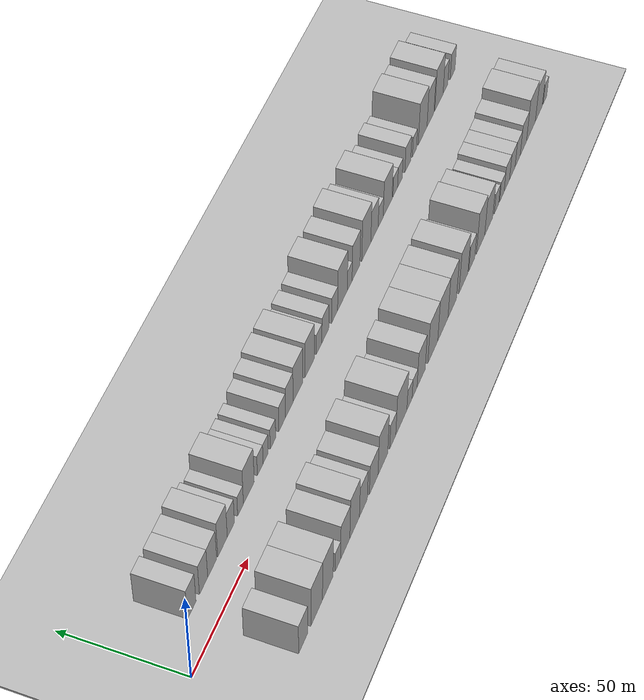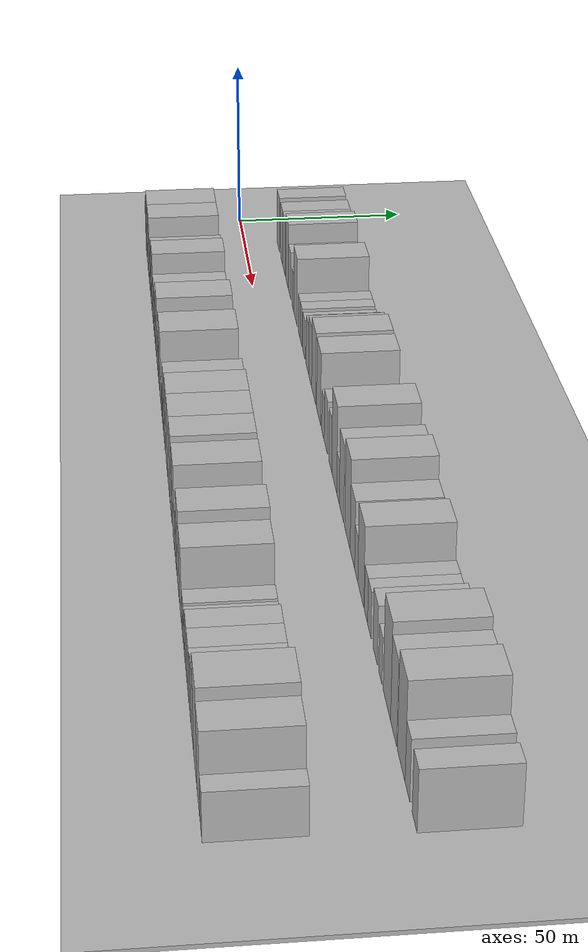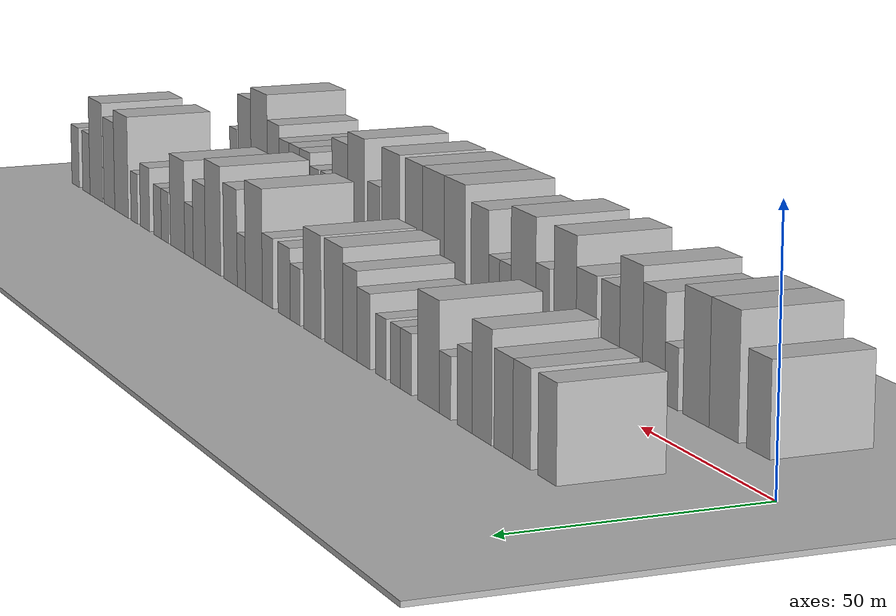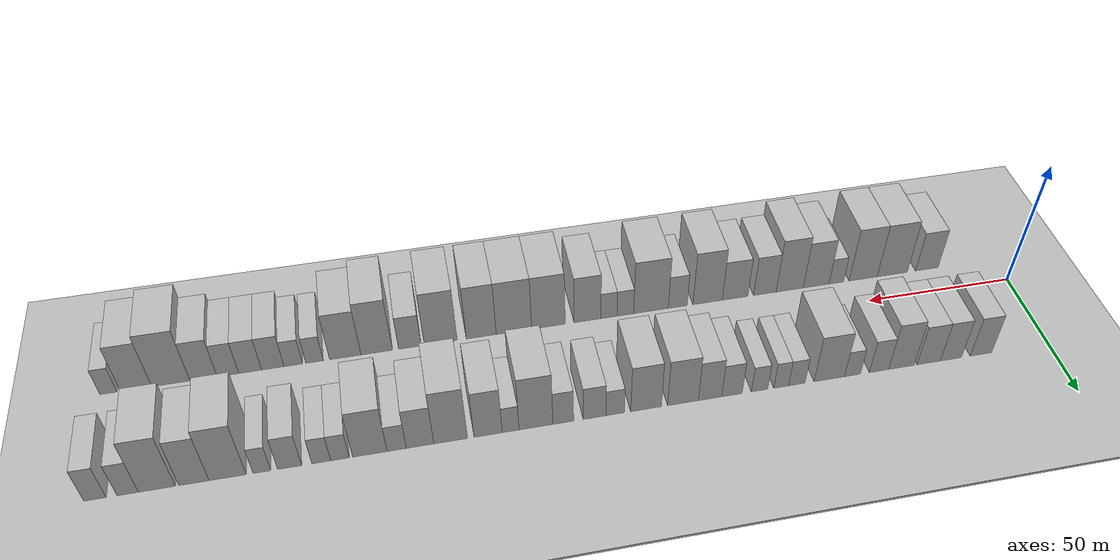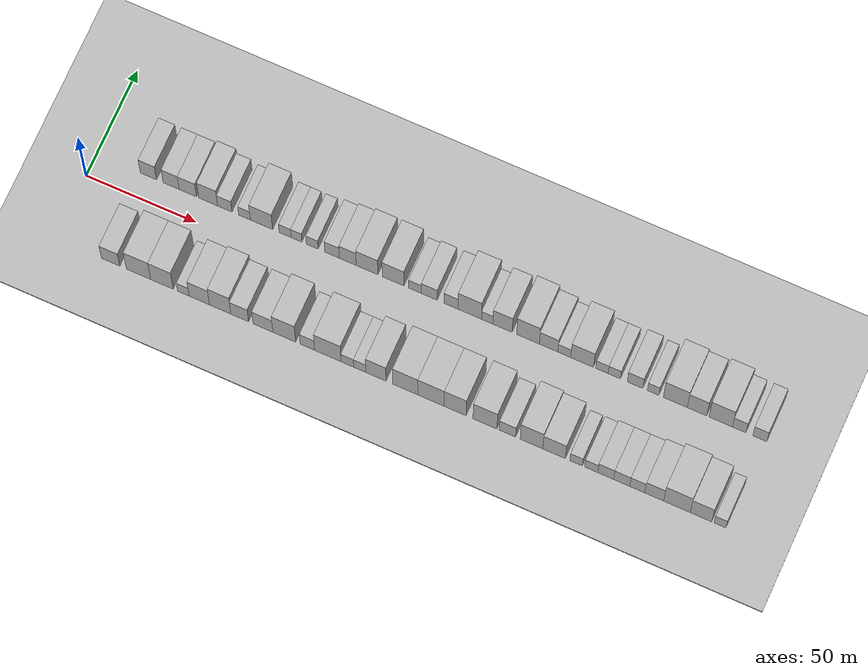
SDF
<?xml version="1.0" encoding="utf-8"?>

<sdf version="1.6">

   <world name="default">

      <gui fullscreen="0">

         <camera name="user_camera">

            <pose>-15 0 4.57585 0 0 0</pose>

            <view_controller>orbit</view_controller>

         </camera>

      </gui>

      <scene>

         <sky>

           <clouds>

             <speed>12</speed>

           </clouds>

         </sky>

         <ambient>0.4 0.4 0.4 1</ambient>

         <background>0.7 0.7 0.7 1</background>

         <shadows>1</shadows>

      </scene>

      <gravity>0 0 -9.8066</gravity>

      <magnetic_field>6e-06 2.3e-05 -4.2e-05</magnetic_field>

      <physics default="0" name="default_physics" type="ode">

         <ode>

            <solver>

               <type>quick</type>

               <iters>10</iters>

               <sor>1.0</sor>

               <use_dynamic_moi_rescaling>0</use_dynamic_moi_rescaling>

            </solver>

            <constraints>

               <cfm>0</cfm>

               <erp>0.2</erp>

               <contact_max_correcting_vel>100</contact_max_correcting_vel>

               <contact_surface_layer>0.001</contact_surface_layer>

            </constraints>

         </ode>

         <max_step_size>0.004</max_step_size>

         <real_time_factor>1</real_time_factor>

         <real_time_update_rate>250</real_time_update_rate>

      </physics>

      <light name="sun" type="directional">

         <cast_shadows>1</cast_shadows>

         <pose>0 0 10 0 0 0</pose>

         <diffuse>0.8 0.8 0.8 1</diffuse>

         <specular>0.2 0.2 0.2 1</specular>

         <attenuation>

            <range>1000</range>

            <constant>0.9</constant>

            <linear>0.01</linear>

            <quadratic>0.001</quadratic>

         </attenuation>

         <direction>-0.5 0.1 -0.9</direction>

      </light>

      <include>

         <name>ground_plane_1</name>

         <uri>model://HANNAS_ground_plane</uri>

         <pose>0 0 0  0 0 0</pose>

      </include>

      <include>

         <name>ground_plane_2</name>

         <uri>model://HANNAS_ground_plane</uri>

         <pose>100 0 0  0 0 0</pose>

      </include>

      <model name="building_1">

         <static>1</static>

         <pose frame="">23.7067 20.0000 0 0.000000 0.000000 1.570796</pose>

         <link name="link">

            <pose frame="">0 0 9.00 0 0 0</pose>

            <collision name="collision">

               <geometry>

                  <box>

                     <size>20.0000 7.4133 18.0000</size>

                  </box>

               </geometry>

               <max_contacts>10</max_contacts>

               <surface>

                  <contact>

                     <ode/>

                  </contact>

                  <bounce/>

                  <friction>

                     <torsional>

                        <ode/>

                     </torsional>

                     <ode/>

                  </friction>

               </surface>

            </collision>

            <visual name="visual">

               <cast_shadows>0</cast_shadows>

               <geometry>

                  <box>

                     <size>20.0000 7.4133 18.0000</size>

                  </box>

               </geometry>

               <material>

                  <script>

                     <uri>model://HANNAS_wall/materials/scripts</uri>

                     <uri>model://HANNAS_wall/materials/textures</uri>

                     <name>vrc/HANNAS_wall</name>

                  </script>

               </material>

            </visual>

            <self_collide>0</self_collide>

            <enable_wind>0</enable_wind>

            <kinematic>0</kinematic>

         </link>

      </model>

      <model name="building_2">

         <static>1</static>

         <pose frame="">34.0660 20.0000 0 0.000000 0.000000 1.570796</pose>

         <link name="link">

            <pose frame="">0 0 9.00 0 0 0</pose>

            <collision name="collision">

               <geometry>

                  <box>

                     <size>20.0000 7.3053 18.0000</size>

                  </box>

               </geometry>

               <max_contacts>10</max_contacts>

               <surface>

                  <contact>

                     <ode/>

                  </contact>

                  <bounce/>

                  <friction>

                     <torsional>

                        <ode/>

                     </torsional>

                     <ode/>

                  </friction>

               </surface>

            </collision>

            <visual name="visual">

               <cast_shadows>0</cast_shadows>

               <geometry>

                  <box>

                     <size>20.0000 7.3053 18.0000</size>

                  </box>

               </geometry>

               <material>

                  <script>

                     <uri>model://HANNAS_wall/materials/scripts</uri>

                     <uri>model://HANNAS_wall/materials/textures</uri>

                     <name>vrc/HANNAS_wall</name>

                  </script>

               </material>

            </visual>

            <self_collide>0</self_collide>

            <enable_wind>0</enable_wind>

            <kinematic>0</kinematic>

         </link>

      </model>

      <model name="building_3">

         <static>1</static>

         <pose frame="">41.6893 20.0000 0 0.000000 0.000000 1.570796</pose>

         <link name="link">

            <pose frame="">0 0 9.00 0 0 0</pose>

            <collision name="collision">

               <geometry>

                  <box>

                     <size>20.0000 7.9413 18.0000</size>

                  </box>

               </geometry>

               <max_contacts>10</max_contacts>

               <surface>

                  <contact>

                     <ode/>

                  </contact>

                  <bounce/>

                  <friction>

                     <torsional>

                        <ode/>

                     </torsional>

                     <ode/>

                  </friction>

               </surface>

            </collision>

            <visual name="visual">

               <cast_shadows>0</cast_shadows>

               <geometry>

                  <box>

                     <size>20.0000 7.9413 18.0000</size>

                  </box>

               </geometry>

               <material>

                  <script>

                     <uri>model://HANNAS_wall/materials/scripts</uri>

                     <uri>model://HANNAS_wall/materials/textures</uri>

                     <name>vrc/HANNAS_wall</name>

                  </script>

               </material>

            </visual>

            <self_collide>0</self_collide>

            <enable_wind>0</enable_wind>

            <kinematic>0</kinematic>

         </link>

      </model>

      <model name="building_4">

         <static>1</static>

         <pose frame="">50.9661 20.0000 0 0.000000 0.000000 1.570796</pose>

         <link name="link">

            <pose frame="">0 0 10.50 0 0 0</pose>

            <collision name="collision">

               <geometry>

                  <box>

                     <size>20.0000 8.6124 21.0000</size>

                  </box>

               </geometry>

               <max_contacts>10</max_contacts>

               <surface>

                  <contact>

                     <ode/>

                  </contact>

                  <bounce/>

                  <friction>

                     <torsional>

                        <ode/>

                     </torsional>

                     <ode/>

                  </friction>

               </surface>

            </collision>

            <visual name="visual">

               <cast_shadows>0</cast_shadows>

               <geometry>

                  <box>

                     <size>20.0000 8.6124 21.0000</size>

                  </box>

               </geometry>

               <material>

                  <script>

                     <uri>model://HANNAS_wall/materials/scripts</uri>

                     <uri>model://HANNAS_wall/materials/textures</uri>

                     <name>vrc/HANNAS_wall</name>

                  </script>

               </material>

            </visual>

            <self_collide>0</self_collide>

            <enable_wind>0</enable_wind>

            <kinematic>0</kinematic>

         </link>

      </model>

      <model name="building_5">

         <static>1</static>

         <pose frame="">58.5462 20.0000 0 0.000000 0.000000 1.570796</pose>

         <link name="link">

            <pose frame="">0 0 7.50 0 0 0</pose>

            <collision name="collision">

               <geometry>

                  <box>

                     <size>20.0000 6.5479 15.0000</size>

                  </box>

               </geometry>

               <max_contacts>10</max_contacts>

               <surface>

                  <contact>

                     <ode/>

                  </contact>

                  <bounce/>

                  <friction>

                     <torsional>

                        <ode/>

                     </torsional>

                     <ode/>

                  </friction>

               </surface>

            </collision>

            <visual name="visual">

               <cast_shadows>0</cast_shadows>

               <geometry>

                  <box>

                     <size>20.0000 6.5479 15.0000</size>

                  </box>

               </geometry>

               <material>

                  <script>

                     <uri>model://HANNAS_wall/materials/scripts</uri>

                     <uri>model://HANNAS_wall/materials/textures</uri>

                     <name>vrc/HANNAS_wall</name>

                  </script>

               </material>

            </visual>

            <self_collide>0</self_collide>

            <enable_wind>0</enable_wind>

            <kinematic>0</kinematic>

         </link>

      </model>

      <model name="building_6">

         <static>1</static>

         <pose frame="">67.4791 20.0000 0 0.000000 0.000000 1.570796</pose>

         <link name="link">

            <pose frame="">0 0 6.00 0 0 0</pose>

            <collision name="collision">

               <geometry>

                  <box>

                     <size>20.0000 5.3178 12.0000</size>

                  </box>

               </geometry>

               <max_contacts>10</max_contacts>

               <surface>

                  <contact>

                     <ode/>

                  </contact>

                  <bounce/>

                  <friction>

                     <torsional>

                        <ode/>

                     </torsional>

                     <ode/>

                  </friction>

               </surface>

            </collision>

            <visual name="visual">

               <cast_shadows>0</cast_shadows>

               <geometry>

                  <box>

                     <size>20.0000 5.3178 12.0000</size>

                  </box>

               </geometry>

               <material>

                  <script>

                     <uri>model://HANNAS_wall/materials/scripts</uri>

                     <uri>model://HANNAS_wall/materials/textures</uri>

                     <name>vrc/HANNAS_wall</name>

                  </script>

               </material>

            </visual>

            <self_collide>0</self_collide>

            <enable_wind>0</enable_wind>

            <kinematic>0</kinematic>

         </link>

      </model>

      <model name="building_7">

         <static>1</static>

         <pose frame="">75.2144 20.0000 0 0.000000 0.000000 1.570796</pose>

         <link name="link">

            <pose frame="">0 0 10.50 0 0 0</pose>

            <collision name="collision">

               <geometry>

                  <box>

                     <size>20.0000 10.1528 21.0000</size>

                  </box>

               </geometry>

               <max_contacts>10</max_contacts>

               <surface>

                  <contact>

                     <ode/>

                  </contact>

                  <bounce/>

                  <friction>

                     <torsional>

                        <ode/>

                     </torsional>

                     <ode/>

                  </friction>

               </surface>

            </collision>

            <visual name="visual">

               <cast_shadows>0</cast_shadows>

               <geometry>

                  <box>

                     <size>20.0000 10.1528 21.0000</size>

                  </box>

               </geometry>

               <material>

                  <script>

                     <uri>model://HANNAS_wall/materials/scripts</uri>

                     <uri>model://HANNAS_wall/materials/textures</uri>

                     <name>vrc/HANNAS_wall</name>

                  </script>

               </material>

            </visual>

            <self_collide>0</self_collide>

            <enable_wind>0</enable_wind>

            <kinematic>0</kinematic>

         </link>

      </model>

      <model name="building_8">

         <static>1</static>

         <pose frame="">86.0134 20.0000 0 0.000000 0.000000 1.570796</pose>

         <link name="link">

            <pose frame="">0 0 6.00 0 0 0</pose>

            <collision name="collision">

               <geometry>

                  <box>

                     <size>20.0000 5.4453 12.0000</size>

                  </box>

               </geometry>

               <max_contacts>10</max_contacts>

               <surface>

                  <contact>

                     <ode/>

                  </contact>

                  <bounce/>

                  <friction>

                     <torsional>

                        <ode/>

                     </torsional>

                     <ode/>

                  </friction>

               </surface>

            </collision>

            <visual name="visual">

               <cast_shadows>0</cast_shadows>

               <geometry>

                  <box>

                     <size>20.0000 5.4453 12.0000</size>

                  </box>

               </geometry>

               <material>

                  <script>

                     <uri>model://HANNAS_wall/materials/scripts</uri>

                     <uri>model://HANNAS_wall/materials/textures</uri>

                     <name>vrc/HANNAS_wall</name>

                  </script>

               </material>

            </visual>

            <self_collide>0</self_collide>

            <enable_wind>0</enable_wind>

            <kinematic>0</kinematic>

         </link>

      </model>

      <model name="building_9">

         <static>1</static>

         <pose frame="">91.1718 20.0000 0 0.000000 0.000000 1.570796</pose>

         <link name="link">

            <pose frame="">0 0 6.00 0 0 0</pose>

            <collision name="collision">

               <geometry>

                  <box>

                     <size>20.0000 4.8716 12.0000</size>

                  </box>

               </geometry>

               <max_contacts>10</max_contacts>

               <surface>

                  <contact>

                     <ode/>

                  </contact>

                  <bounce/>

                  <friction>

                     <torsional>

                        <ode/>

                     </torsional>

                     <ode/>

                  </friction>

               </surface>

            </collision>

            <visual name="visual">

               <cast_shadows>0</cast_shadows>

               <geometry>

                  <box>

                     <size>20.0000 4.8716 12.0000</size>

                  </box>

               </geometry>

               <material>

                  <script>

                     <uri>model://HANNAS_wall/materials/scripts</uri>

                     <uri>model://HANNAS_wall/materials/textures</uri>

                     <name>vrc/HANNAS_wall</name>

                  </script>

               </material>

            </visual>

            <self_collide>0</self_collide>

            <enable_wind>0</enable_wind>

            <kinematic>0</kinematic>

         </link>

      </model>

      <model name="building_10">

         <static>1</static>

         <pose frame="">98.2779 20.0000 0 0.000000 0.000000 1.570796</pose>

         <link name="link">

            <pose frame="">0 0 6.00 0 0 0</pose>

            <collision name="collision">

               <geometry>

                  <box>

                     <size>20.0000 5.3407 12.0000</size>

                  </box>

               </geometry>

               <max_contacts>10</max_contacts>

               <surface>

                  <contact>

                     <ode/>

                  </contact>

                  <bounce/>

                  <friction>

                     <torsional>

                        <ode/>

                     </torsional>

                     <ode/>

                  </friction>

               </surface>

            </collision>

            <visual name="visual">

               <cast_shadows>0</cast_shadows>

               <geometry>

                  <box>

                     <size>20.0000 5.3407 12.0000</size>

                  </box>

               </geometry>

               <material>

                  <script>

                     <uri>model://HANNAS_wall/materials/scripts</uri>

                     <uri>model://HANNAS_wall/materials/textures</uri>

                     <name>vrc/HANNAS_wall</name>

                  </script>

               </material>

            </visual>

            <self_collide>0</self_collide>

            <enable_wind>0</enable_wind>

            <kinematic>0</kinematic>

         </link>

      </model>

      <model name="building_11">

         <static>1</static>

         <pose frame="">107.2684 20.0000 0 0.000000 0.000000 1.570796</pose>

         <link name="link">

            <pose frame="">0 0 7.50 0 0 0</pose>

            <collision name="collision">

               <geometry>

                  <box>

                     <size>20.0000 6.6403 15.0000</size>

                  </box>

               </geometry>

               <max_contacts>10</max_contacts>

               <surface>

                  <contact>

                     <ode/>

                  </contact>

                  <bounce/>

                  <friction>

                     <torsional>

                        <ode/>

                     </torsional>

                     <ode/>

                  </friction>

               </surface>

            </collision>

            <visual name="visual">

               <cast_shadows>0</cast_shadows>

               <geometry>

                  <box>

                     <size>20.0000 6.6403 15.0000</size>

                  </box>

               </geometry>

               <material>

                  <script>

                     <uri>model://HANNAS_wall/materials/scripts</uri>

                     <uri>model://HANNAS_wall/materials/textures</uri>

                     <name>vrc/HANNAS_wall</name>

                  </script>

               </material>

            </visual>

            <self_collide>0</self_collide>

            <enable_wind>0</enable_wind>

            <kinematic>0</kinematic>

         </link>

      </model>

      <model name="building_12">

         <static>1</static>

         <pose frame="">114.3728 20.0000 0 0.000000 0.000000 1.570796</pose>

         <link name="link">

            <pose frame="">0 0 9.00 0 0 0</pose>

            <collision name="collision">

               <geometry>

                  <box>

                     <size>20.0000 7.5686 18.0000</size>

                  </box>

               </geometry>

               <max_contacts>10</max_contacts>

               <surface>

                  <contact>

                     <ode/>

                  </contact>

                  <bounce/>

                  <friction>

                     <torsional>

                        <ode/>

                     </torsional>

                     <ode/>

                  </friction>

               </surface>

            </collision>

            <visual name="visual">

               <cast_shadows>0</cast_shadows>

               <geometry>

                  <box>

                     <size>20.0000 7.5686 18.0000</size>

                  </box>

               </geometry>

               <material>

                  <script>

                     <uri>model://HANNAS_wall/materials/scripts</uri>

                     <uri>model://HANNAS_wall/materials/textures</uri>

                     <name>vrc/HANNAS_wall</name>

                  </script>

               </material>

            </visual>

            <self_collide>0</self_collide>

            <enable_wind>0</enable_wind>

            <kinematic>0</kinematic>

         </link>

      </model>

      <model name="building_13">

         <static>1</static>

         <pose frame="">123.0851 20.0000 0 0.000000 0.000000 1.570796</pose>

         <link name="link">

            <pose frame="">0 0 10.50 0 0 0</pose>

            <collision name="collision">

               <geometry>

                  <box>

                     <size>20.0000 9.8560 21.0000</size>

                  </box>

               </geometry>

               <max_contacts>10</max_contacts>

               <surface>

                  <contact>

                     <ode/>

                  </contact>

                  <bounce/>

                  <friction>

                     <torsional>

                        <ode/>

                     </torsional>

                     <ode/>

                  </friction>

               </surface>

            </collision>

            <visual name="visual">

               <cast_shadows>0</cast_shadows>

               <geometry>

                  <box>

                     <size>20.0000 9.8560 21.0000</size>

                  </box>

               </geometry>

               <material>

                  <script>

                     <uri>model://HANNAS_wall/materials/scripts</uri>

                     <uri>model://HANNAS_wall/materials/textures</uri>

                     <name>vrc/HANNAS_wall</name>

                  </script>

               </material>

            </visual>

            <self_collide>0</self_collide>

            <enable_wind>0</enable_wind>

            <kinematic>0</kinematic>

         </link>

      </model>

      <model name="building_14">

         <static>1</static>

         <pose frame="">134.8923 20.0000 0 0.000000 0.000000 1.570796</pose>

         <link name="link">

            <pose frame="">0 0 10.50 0 0 0</pose>

            <collision name="collision">

               <geometry>

                  <box>

                     <size>20.0000 9.7585 21.0000</size>

                  </box>

               </geometry>

               <max_contacts>10</max_contacts>

               <surface>

                  <contact>

                     <ode/>

                  </contact>

                  <bounce/>

                  <friction>

                     <torsional>

                        <ode/>

                     </torsional>

                     <ode/>

                  </friction>

               </surface>

            </collision>

            <visual name="visual">

               <cast_shadows>0</cast_shadows>

               <geometry>

                  <box>

                     <size>20.0000 9.7585 21.0000</size>

                  </box>

               </geometry>

               <material>

                  <script>

                     <uri>model://HANNAS_wall/materials/scripts</uri>

                     <uri>model://HANNAS_wall/materials/textures</uri>

                     <name>vrc/HANNAS_wall</name>

                  </script>

               </material>

            </visual>

            <self_collide>0</self_collide>

            <enable_wind>0</enable_wind>

            <kinematic>0</kinematic>

         </link>

      </model>

      <model name="building_15">

         <static>1</static>

         <pose frame="">144.6743 20.0000 0 0.000000 0.000000 1.570796</pose>

         <link name="link">

            <pose frame="">0 0 6.00 0 0 0</pose>

            <collision name="collision">

               <geometry>

                  <box>

                     <size>20.0000 5.8056 12.0000</size>

                  </box>

               </geometry>

               <max_contacts>10</max_contacts>

               <surface>

                  <contact>

                     <ode/>

                  </contact>

                  <bounce/>

                  <friction>

                     <torsional>

                        <ode/>

                     </torsional>

                     <ode/>

                  </friction>

               </surface>

            </collision>

            <visual name="visual">

               <cast_shadows>0</cast_shadows>

               <geometry>

                  <box>

                     <size>20.0000 5.8056 12.0000</size>

                  </box>

               </geometry>

               <material>

                  <script>

                     <uri>model://HANNAS_wall/materials/scripts</uri>

                     <uri>model://HANNAS_wall/materials/textures</uri>

                     <name>vrc/HANNAS_wall</name>

                  </script>

               </material>

            </visual>

            <self_collide>0</self_collide>

            <enable_wind>0</enable_wind>

            <kinematic>0</kinematic>

         </link>

      </model>

      <model name="building_16">

         <static>1</static>

         <pose frame="">151.1479 20.0000 0 0.000000 0.000000 1.570796</pose>

         <link name="link">

            <pose frame="">0 0 7.50 0 0 0</pose>

            <collision name="collision">

               <geometry>

                  <box>

                     <size>20.0000 7.1416 15.0000</size>

                  </box>

               </geometry>

               <max_contacts>10</max_contacts>

               <surface>

                  <contact>

                     <ode/>

                  </contact>

                  <bounce/>

                  <friction>

                     <torsional>

                        <ode/>

                     </torsional>

                     <ode/>

                  </friction>

               </surface>

            </collision>

            <visual name="visual">

               <cast_shadows>0</cast_shadows>

               <geometry>

                  <box>

                     <size>20.0000 7.1416 15.0000</size>

                  </box>

               </geometry>

               <material>

                  <script>

                     <uri>model://HANNAS_wall/materials/scripts</uri>

                     <uri>model://HANNAS_wall/materials/textures</uri>

                     <name>vrc/HANNAS_wall</name>

                  </script>

               </material>

            </visual>

            <self_collide>0</self_collide>

            <enable_wind>0</enable_wind>

            <kinematic>0</kinematic>

         </link>

      </model>

      <model name="building_17">

         <static>1</static>

         <pose frame="">160.9357 20.0000 0 0.000000 0.000000 1.570796</pose>

         <link name="link">

            <pose frame="">0 0 7.50 0 0 0</pose>

            <collision name="collision">

               <geometry>

                  <box>

                     <size>20.0000 6.4339 15.0000</size>

                  </box>

               </geometry>

               <max_contacts>10</max_contacts>

               <surface>

                  <contact>

                     <ode/>

                  </contact>

                  <bounce/>

                  <friction>

                     <torsional>

                        <ode/>

                     </torsional>

                     <ode/>

                  </friction>

               </surface>

            </collision>

            <visual name="visual">

               <cast_shadows>0</cast_shadows>

               <geometry>

                  <box>

                     <size>20.0000 6.4339 15.0000</size>

                  </box>

               </geometry>

               <material>

                  <script>

                     <uri>model://HANNAS_wall/materials/scripts</uri>

                     <uri>model://HANNAS_wall/materials/textures</uri>

                     <name>vrc/HANNAS_wall</name>

                  </script>

               </material>

            </visual>

            <self_collide>0</self_collide>

            <enable_wind>0</enable_wind>

            <kinematic>0</kinematic>

         </link>

      </model>

      <model name="building_18">

         <static>1</static>

         <pose frame="">169.3864 20.0000 0 0.000000 0.000000 1.570796</pose>

         <link name="link">

            <pose frame="">0 0 12.00 0 0 0</pose>

            <collision name="collision">

               <geometry>

                  <box>

                     <size>20.0000 10.4674 24.0000</size>

                  </box>

               </geometry>

               <max_contacts>10</max_contacts>

               <surface>

                  <contact>

                     <ode/>

                  </contact>

                  <bounce/>

                  <friction>

                     <torsional>

                        <ode/>

                     </torsional>

                     <ode/>

                  </friction>

               </surface>

            </collision>

            <visual name="visual">

               <cast_shadows>0</cast_shadows>

               <geometry>

                  <box>

                     <size>20.0000 10.4674 24.0000</size>

                  </box>

               </geometry>

               <material>

                  <script>

                     <uri>model://HANNAS_wall/materials/scripts</uri>

                     <uri>model://HANNAS_wall/materials/textures</uri>

                     <name>vrc/HANNAS_wall</name>

                  </script>

               </material>

            </visual>

            <self_collide>0</self_collide>

            <enable_wind>0</enable_wind>

            <kinematic>0</kinematic>

         </link>

      </model>

      <model name="building_19">

         <static>1</static>

         <pose frame="">177.2051 20.0000 0 0.000000 0.000000 1.570796</pose>

         <link name="link">

            <pose frame="">0 0 6.00 0 0 0</pose>

            <collision name="collision">

               <geometry>

                  <box>

                     <size>20.0000 5.1700 12.0000</size>

                  </box>

               </geometry>

               <max_contacts>10</max_contacts>

               <surface>

                  <contact>

                     <ode/>

                  </contact>

                  <bounce/>

                  <friction>

                     <torsional>

                        <ode/>

                     </torsional>

                     <ode/>

                  </friction>

               </surface>

            </collision>

            <visual name="visual">

               <cast_shadows>0</cast_shadows>

               <geometry>

                  <box>

                     <size>20.0000 5.1700 12.0000</size>

                  </box>

               </geometry>

               <material>

                  <script>

                     <uri>model://HANNAS_wall/materials/scripts</uri>

                     <uri>model://HANNAS_wall/materials/textures</uri>

                     <name>vrc/HANNAS_wall</name>

                  </script>

               </material>

            </visual>

            <self_collide>0</self_collide>

            <enable_wind>0</enable_wind>

            <kinematic>0</kinematic>

         </link>

      </model>

      <model name="building_20">

         <static>1</static>

         <pose frame="">184.1034 20.0000 0 0.000000 0.000000 1.570796</pose>

         <link name="link">

            <pose frame="">0 0 10.50 0 0 0</pose>

            <collision name="collision">

               <geometry>

                  <box>

                     <size>20.0000 8.6266 21.0000</size>

                  </box>

               </geometry>

               <max_contacts>10</max_contacts>

               <surface>

                  <contact>

                     <ode/>

                  </contact>

                  <bounce/>

                  <friction>

                     <torsional>

                        <ode/>

                     </torsional>

                     <ode/>

                  </friction>

               </surface>

            </collision>

            <visual name="visual">

               <cast_shadows>0</cast_shadows>

               <geometry>

                  <box>

                     <size>20.0000 8.6266 21.0000</size>

                  </box>

               </geometry>

               <material>

                  <script>

                     <uri>model://HANNAS_wall/materials/scripts</uri>

                     <uri>model://HANNAS_wall/materials/textures</uri>

                     <name>vrc/HANNAS_wall</name>

                  </script>

               </material>

            </visual>

            <self_collide>0</self_collide>

            <enable_wind>0</enable_wind>

            <kinematic>0</kinematic>

         </link>

      </model>

      <model name="building_21">

         <static>1</static>

         <pose frame="">195.5062 20.0000 0 0.000000 0.000000 1.570796</pose>

         <link name="link">

            <pose frame="">0 0 12.00 0 0 0</pose>

            <collision name="collision">

               <geometry>

                  <box>

                     <size>20.0000 10.1790 24.0000</size>

                  </box>

               </geometry>

               <max_contacts>10</max_contacts>

               <surface>

                  <contact>

                     <ode/>

                  </contact>

                  <bounce/>

                  <friction>

                     <torsional>

                        <ode/>

                     </torsional>

                     <ode/>

                  </friction>

               </surface>

            </collision>

            <visual name="visual">

               <cast_shadows>0</cast_shadows>

               <geometry>

                  <box>

                     <size>20.0000 10.1790 24.0000</size>

                  </box>

               </geometry>

               <material>

                  <script>

                     <uri>model://HANNAS_wall/materials/scripts</uri>

                     <uri>model://HANNAS_wall/materials/textures</uri>

                     <name>vrc/HANNAS_wall</name>

                  </script>

               </material>

            </visual>

            <self_collide>0</self_collide>

            <enable_wind>0</enable_wind>

            <kinematic>0</kinematic>

         </link>

      </model>

      <model name="building_22">

         <static>1</static>

         <pose frame="">204.7365 20.0000 0 0.000000 0.000000 1.570796</pose>

         <link name="link">

            <pose frame="">0 0 9.00 0 0 0</pose>

            <collision name="collision">

               <geometry>

                  <box>

                     <size>20.0000 8.2816 18.0000</size>

                  </box>

               </geometry>

               <max_contacts>10</max_contacts>

               <surface>

                  <contact>

                     <ode/>

                  </contact>

                  <bounce/>

                  <friction>

                     <torsional>

                        <ode/>

                     </torsional>

                     <ode/>

                  </friction>

               </surface>

            </collision>

            <visual name="visual">

               <cast_shadows>0</cast_shadows>

               <geometry>

                  <box>

                     <size>20.0000 8.2816 18.0000</size>

                  </box>

               </geometry>

               <material>

                  <script>

                     <uri>model://HANNAS_wall/materials/scripts</uri>

                     <uri>model://HANNAS_wall/materials/textures</uri>

                     <name>vrc/HANNAS_wall</name>

                  </script>

               </material>

            </visual>

            <self_collide>0</self_collide>

            <enable_wind>0</enable_wind>

            <kinematic>0</kinematic>

         </link>

      </model>

      <model name="building_23">

         <static>1</static>

         <pose frame="">211.7590 20.0000 0 0.000000 0.000000 1.570796</pose>

         <link name="link">

            <pose frame="">0 0 6.00 0 0 0</pose>

            <collision name="collision">

               <geometry>

                  <box>

                     <size>20.0000 5.7634 12.0000</size>

                  </box>

               </geometry>

               <max_contacts>10</max_contacts>

               <surface>

                  <contact>

                     <ode/>

                  </contact>

                  <bounce/>

                  <friction>

                     <torsional>

                        <ode/>

                     </torsional>

                     <ode/>

                  </friction>

               </surface>

            </collision>

            <visual name="visual">

               <cast_shadows>0</cast_shadows>

               <geometry>

                  <box>

                     <size>20.0000 5.7634 12.0000</size>

                  </box>

               </geometry>

               <material>

                  <script>

                     <uri>model://HANNAS_wall/materials/scripts</uri>

                     <uri>model://HANNAS_wall/materials/textures</uri>

                     <name>vrc/HANNAS_wall</name>

                  </script>

               </material>

            </visual>

            <self_collide>0</self_collide>

            <enable_wind>0</enable_wind>

            <kinematic>0</kinematic>

         </link>

      </model>

      <model name="building_24">

         <static>1</static>

         <pose frame="">219.7592 20.0000 0 0.000000 0.000000 1.570796</pose>

         <link name="link">

            <pose frame="">0 0 10.50 0 0 0</pose>

            <collision name="collision">

               <geometry>

                  <box>

                     <size>20.0000 10.2370 21.0000</size>

                  </box>

               </geometry>

               <max_contacts>10</max_contacts>

               <surface>

                  <contact>

                     <ode/>

                  </contact>

                  <bounce/>

                  <friction>

                     <torsional>

                        <ode/>

                     </torsional>

                     <ode/>

                  </friction>

               </surface>

            </collision>

            <visual name="visual">

               <cast_shadows>0</cast_shadows>

               <geometry>

                  <box>

                     <size>20.0000 10.2370 21.0000</size>

                  </box>

               </geometry>

               <material>

                  <script>

                     <uri>model://HANNAS_wall/materials/scripts</uri>

                     <uri>model://HANNAS_wall/materials/textures</uri>

                     <name>vrc/HANNAS_wall</name>

                  </script>

               </material>

            </visual>

            <self_collide>0</self_collide>

            <enable_wind>0</enable_wind>

            <kinematic>0</kinematic>

         </link>

      </model>

      <model name="building_25">

         <static>1</static>

         <pose frame="">228.6135 20.0000 0 0.000000 0.000000 1.570796</pose>

         <link name="link">

            <pose frame="">0 0 6.00 0 0 0</pose>

            <collision name="collision">

               <geometry>

                  <box>

                     <size>20.0000 5.4715 12.0000</size>

                  </box>

               </geometry>

               <max_contacts>10</max_contacts>

               <surface>

                  <contact>

                     <ode/>

                  </contact>

                  <bounce/>

                  <friction>

                     <torsional>

                        <ode/>

                     </torsional>

                     <ode/>

                  </friction>

               </surface>

            </collision>

            <visual name="visual">

               <cast_shadows>0</cast_shadows>

               <geometry>

                  <box>

                     <size>20.0000 5.4715 12.0000</size>

                  </box>

               </geometry>

               <material>

                  <script>

                     <uri>model://HANNAS_wall/materials/scripts</uri>

                     <uri>model://HANNAS_wall/materials/textures</uri>

                     <name>vrc/HANNAS_wall</name>

                  </script>

               </material>

            </visual>

            <self_collide>0</self_collide>

            <enable_wind>0</enable_wind>

            <kinematic>0</kinematic>

         </link>

      </model>

      <model name="building_26">

         <static>1</static>

         <pose frame="">234.1191 20.0000 0 0.000000 0.000000 1.570796</pose>

         <link name="link">

            <pose frame="">0 0 6.00 0 0 0</pose>

            <collision name="collision">

               <geometry>

                  <box>

                     <size>20.0000 5.5398 12.0000</size>

                  </box>

               </geometry>

               <max_contacts>10</max_contacts>

               <surface>

                  <contact>

                     <ode/>

                  </contact>

                  <bounce/>

                  <friction>

                     <torsional>

                        <ode/>

                     </torsional>

                     <ode/>

                  </friction>

               </surface>

            </collision>

            <visual name="visual">

               <cast_shadows>0</cast_shadows>

               <geometry>

                  <box>

                     <size>20.0000 5.5398 12.0000</size>

                  </box>

               </geometry>

               <material>

                  <script>

                     <uri>model://HANNAS_wall/materials/scripts</uri>

                     <uri>model://HANNAS_wall/materials/textures</uri>

                     <name>vrc/HANNAS_wall</name>

                  </script>

               </material>

            </visual>

            <self_collide>0</self_collide>

            <enable_wind>0</enable_wind>

            <kinematic>0</kinematic>

         </link>

      </model>

      <model name="building_27">

         <static>1</static>

         <pose frame="">243.3806 20.0000 0 0.000000 0.000000 1.570796</pose>

         <link name="link">

            <pose frame="">0 0 7.50 0 0 0</pose>

            <collision name="collision">

               <geometry>

                  <box>

                     <size>20.0000 6.9831 15.0000</size>

                  </box>

               </geometry>

               <max_contacts>10</max_contacts>

               <surface>

                  <contact>

                     <ode/>

                  </contact>

                  <bounce/>

                  <friction>

                     <torsional>

                        <ode/>

                     </torsional>

                     <ode/>

                  </friction>

               </surface>

            </collision>

            <visual name="visual">

               <cast_shadows>0</cast_shadows>

               <geometry>

                  <box>

                     <size>20.0000 6.9831 15.0000</size>

                  </box>

               </geometry>

               <material>

                  <script>

                     <uri>model://HANNAS_wall/materials/scripts</uri>

                     <uri>model://HANNAS_wall/materials/textures</uri>

                     <name>vrc/HANNAS_wall</name>

                  </script>

               </material>

            </visual>

            <self_collide>0</self_collide>

            <enable_wind>0</enable_wind>

            <kinematic>0</kinematic>

         </link>

      </model>

      <model name="building_28">

         <static>1</static>

         <pose frame="">251.4328 20.0000 0 0.000000 0.000000 1.570796</pose>

         <link name="link">

            <pose frame="">0 0 6.00 0 0 0</pose>

            <collision name="collision">

               <geometry>

                  <box>

                     <size>20.0000 5.1213 12.0000</size>

                  </box>

               </geometry>

               <max_contacts>10</max_contacts>

               <surface>

                  <contact>

                     <ode/>

                  </contact>

                  <bounce/>

                  <friction>

                     <torsional>

                        <ode/>

                     </torsional>

                     <ode/>

                  </friction>

               </surface>

            </collision>

            <visual name="visual">

               <cast_shadows>0</cast_shadows>

               <geometry>

                  <box>

                     <size>20.0000 5.1213 12.0000</size>

                  </box>

               </geometry>

               <material>

                  <script>

                     <uri>model://HANNAS_wall/materials/scripts</uri>

                     <uri>model://HANNAS_wall/materials/textures</uri>

                     <name>vrc/HANNAS_wall</name>

                  </script>

               </material>

            </visual>

            <self_collide>0</self_collide>

            <enable_wind>0</enable_wind>

            <kinematic>0</kinematic>

         </link>

      </model>

      <model name="building_29">

         <static>1</static>

         <pose frame="">261.3288 20.0000 0 0.000000 0.000000 1.570796</pose>

         <link name="link">

            <pose frame="">0 0 12.00 0 0 0</pose>

            <collision name="collision">

               <geometry>

                  <box>

                     <size>20.0000 10.6708 24.0000</size>

                  </box>

               </geometry>

               <max_contacts>10</max_contacts>

               <surface>

                  <contact>

                     <ode/>

                  </contact>

                  <bounce/>

                  <friction>

                     <torsional>

                        <ode/>

                     </torsional>

                     <ode/>

                  </friction>

               </surface>

            </collision>

            <visual name="visual">

               <cast_shadows>0</cast_shadows>

               <geometry>

                  <box>

                     <size>20.0000 10.6708 24.0000</size>

                  </box>

               </geometry>

               <material>

                  <script>

                     <uri>model://HANNAS_wall/materials/scripts</uri>

                     <uri>model://HANNAS_wall/materials/textures</uri>

                     <name>vrc/HANNAS_wall</name>

                  </script>

               </material>

            </visual>

            <self_collide>0</self_collide>

            <enable_wind>0</enable_wind>

            <kinematic>0</kinematic>

         </link>

      </model>

      <model name="building_30">

         <static>1</static>

         <pose frame="">270.9674 20.0000 0 0.000000 0.000000 1.570796</pose>

         <link name="link">

            <pose frame="">0 0 10.50 0 0 0</pose>

            <collision name="collision">

               <geometry>

                  <box>

                     <size>20.0000 8.6062 21.0000</size>

                  </box>

               </geometry>

               <max_contacts>10</max_contacts>

               <surface>

                  <contact>

                     <ode/>

                  </contact>

                  <bounce/>

                  <friction>

                     <torsional>

                        <ode/>

                     </torsional>

                     <ode/>

                  </friction>

               </surface>

            </collision>

            <visual name="visual">

               <cast_shadows>0</cast_shadows>

               <geometry>

                  <box>

                     <size>20.0000 8.6062 21.0000</size>

                  </box>

               </geometry>

               <material>

                  <script>

                     <uri>model://HANNAS_wall/materials/scripts</uri>

                     <uri>model://HANNAS_wall/materials/textures</uri>

                     <name>vrc/HANNAS_wall</name>

                  </script>

               </material>

            </visual>

            <self_collide>0</self_collide>

            <enable_wind>0</enable_wind>

            <kinematic>0</kinematic>

         </link>

      </model>

      <model name="building_31">

         <static>1</static>

         <pose frame="">281.4899 20.0000 0 0.000000 0.000000 1.570796</pose>

         <link name="link">

            <pose frame="">0 0 12.00 0 0 0</pose>

            <collision name="collision">

               <geometry>

                  <box>

                     <size>20.0000 10.4389 24.0000</size>

                  </box>

               </geometry>

               <max_contacts>10</max_contacts>

               <surface>

                  <contact>

                     <ode/>

                  </contact>

                  <bounce/>

                  <friction>

                     <torsional>

                        <ode/>

                     </torsional>

                     <ode/>

                  </friction>

               </surface>

            </collision>

            <visual name="visual">

               <cast_shadows>0</cast_shadows>

               <geometry>

                  <box>

                     <size>20.0000 10.4389 24.0000</size>

                  </box>

               </geometry>

               <material>

                  <script>

                     <uri>model://HANNAS_wall/materials/scripts</uri>

                     <uri>model://HANNAS_wall/materials/textures</uri>

                     <name>vrc/HANNAS_wall</name>

                  </script>

               </material>

            </visual>

            <self_collide>0</self_collide>

            <enable_wind>0</enable_wind>

            <kinematic>0</kinematic>

         </link>

      </model>

      <model name="building_32">

         <static>1</static>

         <pose frame="">289.7101 20.0000 0 0.000000 0.000000 1.570796</pose>

         <link name="link">

            <pose frame="">0 0 7.50 0 0 0</pose>

            <collision name="collision">

               <geometry>

                  <box>

                     <size>20.0000 6.0015 15.0000</size>

                  </box>

               </geometry>

               <max_contacts>10</max_contacts>

               <surface>

                  <contact>

                     <ode/>

                  </contact>

                  <bounce/>

                  <friction>

                     <torsional>

                        <ode/>

                     </torsional>

                     <ode/>

                  </friction>

               </surface>

            </collision>

            <visual name="visual">

               <cast_shadows>0</cast_shadows>

               <geometry>

                  <box>

                     <size>20.0000 6.0015 15.0000</size>

                  </box>

               </geometry>

               <material>

                  <script>

                     <uri>model://HANNAS_wall/materials/scripts</uri>

                     <uri>model://HANNAS_wall/materials/textures</uri>

                     <name>vrc/HANNAS_wall</name>

                  </script>

               </material>

            </visual>

            <self_collide>0</self_collide>

            <enable_wind>0</enable_wind>

            <kinematic>0</kinematic>

         </link>

      </model>

      <model name="building_33">

         <static>1</static>

         <pose frame="">298.8241 20.0000 0 0.000000 0.000000 1.570796</pose>

         <link name="link">

            <pose frame="">0 0 7.50 0 0 0</pose>

            <collision name="collision">

               <geometry>

                  <box>

                     <size>20.0000 6.2265 15.0000</size>

                  </box>

               </geometry>

               <max_contacts>10</max_contacts>

               <surface>

                  <contact>

                     <ode/>

                  </contact>

                  <bounce/>

                  <friction>

                     <torsional>

                        <ode/>

                     </torsional>

                     <ode/>

                  </friction>

               </surface>

            </collision>

            <visual name="visual">

               <cast_shadows>0</cast_shadows>

               <geometry>

                  <box>

                     <size>20.0000 6.2265 15.0000</size>

                  </box>

               </geometry>

               <material>

                  <script>

                     <uri>model://HANNAS_wall/materials/scripts</uri>

                     <uri>model://HANNAS_wall/materials/textures</uri>

                     <name>vrc/HANNAS_wall</name>

                  </script>

               </material>

            </visual>

            <self_collide>0</self_collide>

            <enable_wind>0</enable_wind>

            <kinematic>0</kinematic>

         </link>

      </model>

      <model name="building_34">

         <static>1</static>

         <pose frame="">25.1839 -20.0000 0 0.000000 0.000000 1.570796</pose>

         <link name="link">

            <pose frame="">0 0 9.00 0 0 0</pose>

            <collision name="collision">

               <geometry>

                  <box>

                     <size>20.0000 8.3678 18.0000</size>

                  </box>

               </geometry>

               <max_contacts>10</max_contacts>

               <surface>

                  <contact>

                     <ode/>

                  </contact>

                  <bounce/>

                  <friction>

                     <torsional>

                        <ode/>

                     </torsional>

                     <ode/>

                  </friction>

               </surface>

            </collision>

            <visual name="visual">

               <cast_shadows>0</cast_shadows>

               <geometry>

                  <box>

                     <size>20.0000 8.3678 18.0000</size>

                  </box>

               </geometry>

               <material>

                  <script>

                     <uri>model://HANNAS_wall/materials/scripts</uri>

                     <uri>model://HANNAS_wall/materials/textures</uri>

                     <name>vrc/HANNAS_wall</name>

                  </script>

               </material>

            </visual>

            <self_collide>0</self_collide>

            <enable_wind>0</enable_wind>

            <kinematic>0</kinematic>

         </link>

      </model>

      <model name="building_35">

         <static>1</static>

         <pose frame="">37.8844 -20.0000 0 0.000000 0.000000 1.570796</pose>

         <link name="link">

            <pose frame="">0 0 12.00 0 0 0</pose>

            <collision name="collision">

               <geometry>

                  <box>

                     <size>20.0000 11.0331 24.0000</size>

                  </box>

               </geometry>

               <max_contacts>10</max_contacts>

               <surface>

                  <contact>

                     <ode/>

                  </contact>

                  <bounce/>

                  <friction>

                     <torsional>

                        <ode/>

                     </torsional>

                     <ode/>

                  </friction>

               </surface>

            </collision>

            <visual name="visual">

               <cast_shadows>0</cast_shadows>

               <geometry>

                  <box>

                     <size>20.0000 11.0331 24.0000</size>

                  </box>

               </geometry>

               <material>

                  <script>

                     <uri>model://HANNAS_wall/materials/scripts</uri>

                     <uri>model://HANNAS_wall/materials/textures</uri>

                     <name>vrc/HANNAS_wall</name>

                  </script>

               </material>

            </visual>

            <self_collide>0</self_collide>

            <enable_wind>0</enable_wind>

            <kinematic>0</kinematic>

         </link>

      </model>

      <model name="building_36">

         <static>1</static>

         <pose frame="">48.5045 -20.0000 0 0.000000 0.000000 1.570796</pose>

         <link name="link">

            <pose frame="">0 0 12.00 0 0 0</pose>

            <collision name="collision">

               <geometry>

                  <box>

                     <size>20.0000 10.2072 24.0000</size>

                  </box>

               </geometry>

               <max_contacts>10</max_contacts>

               <surface>

                  <contact>

                     <ode/>

                  </contact>

                  <bounce/>

                  <friction>

                     <torsional>

                        <ode/>

                     </torsional>

                     <ode/>

                  </friction>

               </surface>

            </collision>

            <visual name="visual">

               <cast_shadows>0</cast_shadows>

               <geometry>

                  <box>

                     <size>20.0000 10.2072 24.0000</size>

                  </box>

               </geometry>

               <material>

                  <script>

                     <uri>model://HANNAS_wall/materials/scripts</uri>

                     <uri>model://HANNAS_wall/materials/textures</uri>

                     <name>vrc/HANNAS_wall</name>

                  </script>

               </material>

            </visual>

            <self_collide>0</self_collide>

            <enable_wind>0</enable_wind>

            <kinematic>0</kinematic>

         </link>

      </model>

      <model name="building_37">

         <static>1</static>

         <pose frame="">58.2221 -20.0000 0 0.000000 0.000000 1.570796</pose>

         <link name="link">

            <pose frame="">0 0 6.00 0 0 0</pose>

            <collision name="collision">

               <geometry>

                  <box>

                     <size>20.0000 5.2281 12.0000</size>

                  </box>

               </geometry>

               <max_contacts>10</max_contacts>

               <surface>

                  <contact>

                     <ode/>

                  </contact>

                  <bounce/>

                  <friction>

                     <torsional>

                        <ode/>

                     </torsional>

                     <ode/>

                  </friction>

               </surface>

            </collision>

            <visual name="visual">

               <cast_shadows>0</cast_shadows>

               <geometry>

                  <box>

                     <size>20.0000 5.2281 12.0000</size>

                  </box>

               </geometry>

               <material>

                  <script>

                     <uri>model://HANNAS_wall/materials/scripts</uri>

                     <uri>model://HANNAS_wall/materials/textures</uri>

                     <name>vrc/HANNAS_wall</name>

                  </script>

               </material>

            </visual>

            <self_collide>0</self_collide>

            <enable_wind>0</enable_wind>

            <kinematic>0</kinematic>

         </link>

      </model>

      <model name="building_38">

         <static>1</static>

         <pose frame="">65.4593 -20.0000 0 0.000000 0.000000 1.570796</pose>

         <link name="link">

            <pose frame="">0 0 10.50 0 0 0</pose>

            <collision name="collision">

               <geometry>

                  <box>

                     <size>20.0000 9.2462 21.0000</size>

                  </box>

               </geometry>

               <max_contacts>10</max_contacts>

               <surface>

                  <contact>

                     <ode/>

                  </contact>

                  <bounce/>

                  <friction>

                     <torsional>

                        <ode/>

                     </torsional>

                     <ode/>

                  </friction>

               </surface>

            </collision>

            <visual name="visual">

               <cast_shadows>0</cast_shadows>

               <geometry>

                  <box>

                     <size>20.0000 9.2462 21.0000</size>

                  </box>

               </geometry>

               <material>

                  <script>

                     <uri>model://HANNAS_wall/materials/scripts</uri>

                     <uri>model://HANNAS_wall/materials/textures</uri>

                     <name>vrc/HANNAS_wall</name>

                  </script>

               </material>

            </visual>

            <self_collide>0</self_collide>

            <enable_wind>0</enable_wind>

            <kinematic>0</kinematic>

         </link>

      </model>

      <model name="building_39">

         <static>1</static>

         <pose frame="">74.9017 -20.0000 0 0.000000 0.000000 1.570796</pose>

         <link name="link">

            <pose frame="">0 0 12.00 0 0 0</pose>

            <collision name="collision">

               <geometry>

                  <box>

                     <size>20.0000 9.6387 24.0000</size>

                  </box>

               </geometry>

               <max_contacts>10</max_contacts>

               <surface>

                  <contact>

                     <ode/>

                  </contact>

                  <bounce/>

                  <friction>

                     <torsional>

                        <ode/>

                     </torsional>

                     <ode/>

                  </friction>

               </surface>

            </collision>

            <visual name="visual">

               <cast_shadows>0</cast_shadows>

               <geometry>

                  <box>

                     <size>20.0000 9.6387 24.0000</size>

                  </box>

               </geometry>

               <material>

                  <script>

                     <uri>model://HANNAS_wall/materials/scripts</uri>

                     <uri>model://HANNAS_wall/materials/textures</uri>

                     <name>vrc/HANNAS_wall</name>

                  </script>

               </material>

            </visual>

            <self_collide>0</self_collide>

            <enable_wind>0</enable_wind>

            <kinematic>0</kinematic>

         </link>

      </model>

      <model name="building_40">

         <static>1</static>

         <pose frame="">83.7259 -20.0000 0 0.000000 0.000000 1.570796</pose>

         <link name="link">

            <pose frame="">0 0 9.00 0 0 0</pose>

            <collision name="collision">

               <geometry>

                  <box>

                     <size>20.0000 8.0097 18.0000</size>

                  </box>

               </geometry>

               <max_contacts>10</max_contacts>

               <surface>

                  <contact>

                     <ode/>

                  </contact>

                  <bounce/>

                  <friction>

                     <torsional>

                        <ode/>

                     </torsional>

                     <ode/>

                  </friction>

               </surface>

            </collision>

            <visual name="visual">

               <cast_shadows>0</cast_shadows>

               <geometry>

                  <box>

                     <size>20.0000 8.0097 18.0000</size>

                  </box>

               </geometry>

               <material>

                  <script>

                     <uri>model://HANNAS_wall/materials/scripts</uri>

                     <uri>model://HANNAS_wall/materials/textures</uri>

                     <name>vrc/HANNAS_wall</name>

                  </script>

               </material>

            </visual>

            <self_collide>0</self_collide>

            <enable_wind>0</enable_wind>

            <kinematic>0</kinematic>

         </link>

      </model>

      <model name="building_41">

         <static>1</static>

         <pose frame="">94.2265 -20.0000 0 0.000000 0.000000 1.570796</pose>

         <link name="link">

            <pose frame="">0 0 9.00 0 0 0</pose>

            <collision name="collision">

               <geometry>

                  <box>

                     <size>20.0000 8.9914 18.0000</size>

                  </box>

               </geometry>

               <max_contacts>10</max_contacts>

               <surface>

                  <contact>

                     <ode/>

                  </contact>

                  <bounce/>

                  <friction>

                     <torsional>

                        <ode/>

                     </torsional>

                     <ode/>

                  </friction>

               </surface>

            </collision>

            <visual name="visual">

               <cast_shadows>0</cast_shadows>

               <geometry>

                  <box>

                     <size>20.0000 8.9914 18.0000</size>

                  </box>

               </geometry>

               <material>

                  <script>

                     <uri>model://HANNAS_wall/materials/scripts</uri>

                     <uri>model://HANNAS_wall/materials/textures</uri>

                     <name>vrc/HANNAS_wall</name>

                  </script>

               </material>

            </visual>

            <self_collide>0</self_collide>

            <enable_wind>0</enable_wind>

            <kinematic>0</kinematic>

         </link>

      </model>

      <model name="building_42">

         <static>1</static>

         <pose frame="">103.8564 -20.0000 0 0.000000 0.000000 1.570796</pose>

         <link name="link">

            <pose frame="">0 0 12.00 0 0 0</pose>

            <collision name="collision">

               <geometry>

                  <box>

                     <size>20.0000 10.2684 24.0000</size>

                  </box>

               </geometry>

               <max_contacts>10</max_contacts>

               <surface>

                  <contact>

                     <ode/>

                  </contact>

                  <bounce/>

                  <friction>

                     <torsional>

                        <ode/>

                     </torsional>

                     <ode/>

                  </friction>

               </surface>

            </collision>

            <visual name="visual">

               <cast_shadows>0</cast_shadows>

               <geometry>

                  <box>

                     <size>20.0000 10.2684 24.0000</size>

                  </box>

               </geometry>

               <material>

                  <script>

                     <uri>model://HANNAS_wall/materials/scripts</uri>

                     <uri>model://HANNAS_wall/materials/textures</uri>

                     <name>vrc/HANNAS_wall</name>

                  </script>

               </material>

            </visual>

            <self_collide>0</self_collide>

            <enable_wind>0</enable_wind>

            <kinematic>0</kinematic>

         </link>

      </model>

      <model name="building_43">

         <static>1</static>

         <pose frame="">114.2496 -20.0000 0 0.000000 0.000000 1.570796</pose>

         <link name="link">

            <pose frame="">0 0 7.50 0 0 0</pose>

            <collision name="collision">

               <geometry>

                  <box>

                     <size>20.0000 6.5179 15.0000</size>

                  </box>

               </geometry>

               <max_contacts>10</max_contacts>

               <surface>

                  <contact>

                     <ode/>

                  </contact>

                  <bounce/>

                  <friction>

                     <torsional>

                        <ode/>

                     </torsional>

                     <ode/>

                  </friction>

               </surface>

            </collision>

            <visual name="visual">

               <cast_shadows>0</cast_shadows>

               <geometry>

                  <box>

                     <size>20.0000 6.5179 15.0000</size>

                  </box>

               </geometry>

               <material>

                  <script>

                     <uri>model://HANNAS_wall/materials/scripts</uri>

                     <uri>model://HANNAS_wall/materials/textures</uri>

                     <name>vrc/HANNAS_wall</name>

                  </script>

               </material>

            </visual>

            <self_collide>0</self_collide>

            <enable_wind>0</enable_wind>

            <kinematic>0</kinematic>

         </link>

      </model>

      <model name="building_44">

         <static>1</static>

         <pose frame="">123.4821 -20.0000 0 0.000000 0.000000 1.570796</pose>

         <link name="link">

            <pose frame="">0 0 12.00 0 0 0</pose>

            <collision name="collision">

               <geometry>

                  <box>

                     <size>20.0000 11.9471 24.0000</size>

                  </box>

               </geometry>

               <max_contacts>10</max_contacts>

               <surface>

                  <contact>

                     <ode/>

                  </contact>

                  <bounce/>

                  <friction>

                     <torsional>

                        <ode/>

                     </torsional>

                     <ode/>

                  </friction>

               </surface>

            </collision>

            <visual name="visual">

               <cast_shadows>0</cast_shadows>

               <geometry>

                  <box>

                     <size>20.0000 11.9471 24.0000</size>

                  </box>

               </geometry>

               <material>

                  <script>

                     <uri>model://HANNAS_wall/materials/scripts</uri>

                     <uri>model://HANNAS_wall/materials/textures</uri>

                     <name>vrc/HANNAS_wall</name>

                  </script>

               </material>

            </visual>

            <self_collide>0</self_collide>

            <enable_wind>0</enable_wind>

            <kinematic>0</kinematic>

         </link>

      </model>

      <model name="building_45">

         <static>1</static>

         <pose frame="">132.2777 -20.0000 0 0.000000 0.000000 1.570796</pose>

         <link name="link">

            <pose frame="">0 0 6.00 0 0 0</pose>

            <collision name="collision">

               <geometry>

                  <box>

                     <size>20.0000 5.6442 12.0000</size>

                  </box>

               </geometry>

               <max_contacts>10</max_contacts>

               <surface>

                  <contact>

                     <ode/>

                  </contact>

                  <bounce/>

                  <friction>

                     <torsional>

                        <ode/>

                     </torsional>

                     <ode/>

                  </friction>

               </surface>

            </collision>

            <visual name="visual">

               <cast_shadows>0</cast_shadows>

               <geometry>

                  <box>

                     <size>20.0000 5.6442 12.0000</size>

                  </box>

               </geometry>

               <material>

                  <script>

                     <uri>model://HANNAS_wall/materials/scripts</uri>

                     <uri>model://HANNAS_wall/materials/textures</uri>

                     <name>vrc/HANNAS_wall</name>

                  </script>

               </material>

            </visual>

            <self_collide>0</self_collide>

            <enable_wind>0</enable_wind>

            <kinematic>0</kinematic>

         </link>

      </model>

      <model name="building_46">

         <static>1</static>

         <pose frame="">137.8604 -20.0000 0 0.000000 0.000000 1.570796</pose>

         <link name="link">

            <pose frame="">0 0 6.00 0 0 0</pose>

            <collision name="collision">

               <geometry>

                  <box>

                     <size>20.0000 5.5211 12.0000</size>

                  </box>

               </geometry>

               <max_contacts>10</max_contacts>

               <surface>

                  <contact>

                     <ode/>

                  </contact>

                  <bounce/>

                  <friction>

                     <torsional>

                        <ode/>

                     </torsional>

                     <ode/>

                  </friction>

               </surface>

            </collision>

            <visual name="visual">

               <cast_shadows>0</cast_shadows>

               <geometry>

                  <box>

                     <size>20.0000 5.5211 12.0000</size>

                  </box>

               </geometry>

               <material>

                  <script>

                     <uri>model://HANNAS_wall/materials/scripts</uri>

                     <uri>model://HANNAS_wall/materials/textures</uri>

                     <name>vrc/HANNAS_wall</name>

                  </script>

               </material>

            </visual>

            <self_collide>0</self_collide>

            <enable_wind>0</enable_wind>

            <kinematic>0</kinematic>

         </link>

      </model>

      <model name="building_47">

         <static>1</static>

         <pose frame="">145.1463 -20.0000 0 0.000000 0.000000 1.570796</pose>

         <link name="link">

            <pose frame="">0 0 10.50 0 0 0</pose>

            <collision name="collision">

               <geometry>

                  <box>

                     <size>20.0000 9.0507 21.0000</size>

                  </box>

               </geometry>

               <max_contacts>10</max_contacts>

               <surface>

                  <contact>

                     <ode/>

                  </contact>

                  <bounce/>

                  <friction>

                     <torsional>

                        <ode/>

                     </torsional>

                     <ode/>

                  </friction>

               </surface>

            </collision>

            <visual name="visual">

               <cast_shadows>0</cast_shadows>

               <geometry>

                  <box>

                     <size>20.0000 9.0507 21.0000</size>

                  </box>

               </geometry>

               <material>

                  <script>

                     <uri>model://HANNAS_wall/materials/scripts</uri>

                     <uri>model://HANNAS_wall/materials/textures</uri>

                     <name>vrc/HANNAS_wall</name>

                  </script>

               </material>

            </visual>

            <self_collide>0</self_collide>

            <enable_wind>0</enable_wind>

            <kinematic>0</kinematic>

         </link>

      </model>

      <model name="building_48">

         <static>1</static>

         <pose frame="">158.2835 -20.0000 0 0.000000 0.000000 1.570796</pose>

         <link name="link">

            <pose frame="">0 0 12.00 0 0 0</pose>

            <collision name="collision">

               <geometry>

                  <box>

                     <size>20.0000 11.2238 24.0000</size>

                  </box>

               </geometry>

               <max_contacts>10</max_contacts>

               <surface>

                  <contact>

                     <ode/>

                  </contact>

                  <bounce/>

                  <friction>

                     <torsional>

                        <ode/>

                     </torsional>

                     <ode/>

                  </friction>

               </surface>

            </collision>

            <visual name="visual">

               <cast_shadows>0</cast_shadows>

               <geometry>

                  <box>

                     <size>20.0000 11.2238 24.0000</size>

                  </box>

               </geometry>

               <material>

                  <script>

                     <uri>model://HANNAS_wall/materials/scripts</uri>

                     <uri>model://HANNAS_wall/materials/textures</uri>

                     <name>vrc/HANNAS_wall</name>

                  </script>

               </material>

            </visual>

            <self_collide>0</self_collide>

            <enable_wind>0</enable_wind>

            <kinematic>0</kinematic>

         </link>

      </model>

      <model name="building_49">

         <static>1</static>

         <pose frame="">169.7892 -20.0000 0 0.000000 0.000000 1.570796</pose>

         <link name="link">

            <pose frame="">0 0 12.00 0 0 0</pose>

            <collision name="collision">

               <geometry>

                  <box>

                     <size>20.0000 11.7876 24.0000</size>

                  </box>

               </geometry>

               <max_contacts>10</max_contacts>

               <surface>

                  <contact>

                     <ode/>

                  </contact>

                  <bounce/>

                  <friction>

                     <torsional>

                        <ode/>

                     </torsional>

                     <ode/>

                  </friction>

               </surface>

            </collision>

            <visual name="visual">

               <cast_shadows>0</cast_shadows>

               <geometry>

                  <box>

                     <size>20.0000 11.7876 24.0000</size>

                  </box>

               </geometry>

               <material>

                  <script>

                     <uri>model://HANNAS_wall/materials/scripts</uri>

                     <uri>model://HANNAS_wall/materials/textures</uri>

                     <name>vrc/HANNAS_wall</name>

                  </script>

               </material>

            </visual>

            <self_collide>0</self_collide>

            <enable_wind>0</enable_wind>

            <kinematic>0</kinematic>

         </link>

      </model>

      <model name="building_50">

         <static>1</static>

         <pose frame="">180.6211 -20.0000 0 0.000000 0.000000 1.570796</pose>

         <link name="link">

            <pose frame="">0 0 12.00 0 0 0</pose>

            <collision name="collision">

               <geometry>

                  <box>

                     <size>20.0000 9.8762 24.0000</size>

                  </box>

               </geometry>

               <max_contacts>10</max_contacts>

               <surface>

                  <contact>

                     <ode/>

                  </contact>

                  <bounce/>

                  <friction>

                     <torsional>

                        <ode/>

                     </torsional>

                     <ode/>

                  </friction>

               </surface>

            </collision>

            <visual name="visual">

               <cast_shadows>0</cast_shadows>

               <geometry>

                  <box>

                     <size>20.0000 9.8762 24.0000</size>

                  </box>

               </geometry>

               <material>

                  <script>

                     <uri>model://HANNAS_wall/materials/scripts</uri>

                     <uri>model://HANNAS_wall/materials/textures</uri>

                     <name>vrc/HANNAS_wall</name>

                  </script>

               </material>

            </visual>

            <self_collide>0</self_collide>

            <enable_wind>0</enable_wind>

            <kinematic>0</kinematic>

         </link>

      </model>

      <model name="building_51">

         <static>1</static>

         <pose frame="">193.9153 -20.0000 0 0.000000 0.000000 1.570796</pose>

         <link name="link">

            <pose frame="">0 0 12.00 0 0 0</pose>

            <collision name="collision">

               <geometry>

                  <box>

                     <size>20.0000 10.7122 24.0000</size>

                  </box>

               </geometry>

               <max_contacts>10</max_contacts>

               <surface>

                  <contact>

                     <ode/>

                  </contact>

                  <bounce/>

                  <friction>

                     <torsional>

                        <ode/>

                     </torsional>

                     <ode/>

                  </friction>

               </surface>

            </collision>

            <visual name="visual">

               <cast_shadows>0</cast_shadows>

               <geometry>

                  <box>

                     <size>20.0000 10.7122 24.0000</size>

                  </box>

               </geometry>

               <material>

                  <script>

                     <uri>model://HANNAS_wall/materials/scripts</uri>

                     <uri>model://HANNAS_wall/materials/textures</uri>

                     <name>vrc/HANNAS_wall</name>

                  </script>

               </material>

            </visual>

            <self_collide>0</self_collide>

            <enable_wind>0</enable_wind>

            <kinematic>0</kinematic>

         </link>

      </model>

      <model name="building_52">

         <static>1</static>

         <pose frame="">203.9388 -20.0000 0 0.000000 0.000000 1.570796</pose>

         <link name="link">

            <pose frame="">0 0 7.50 0 0 0</pose>

            <collision name="collision">

               <geometry>

                  <box>

                     <size>20.0000 7.3349 15.0000</size>

                  </box>

               </geometry>

               <max_contacts>10</max_contacts>

               <surface>

                  <contact>

                     <ode/>

                  </contact>

                  <bounce/>

                  <friction>

                     <torsional>

                        <ode/>

                     </torsional>

                     <ode/>

                  </friction>

               </surface>

            </collision>

            <visual name="visual">

               <cast_shadows>0</cast_shadows>

               <geometry>

                  <box>

                     <size>20.0000 7.3349 15.0000</size>

                  </box>

               </geometry>

               <material>

                  <script>

                     <uri>model://HANNAS_wall/materials/scripts</uri>

                     <uri>model://HANNAS_wall/materials/textures</uri>

                     <name>vrc/HANNAS_wall</name>

                  </script>

               </material>

            </visual>

            <self_collide>0</self_collide>

            <enable_wind>0</enable_wind>

            <kinematic>0</kinematic>

         </link>

      </model>

      <model name="building_53">

         <static>1</static>

         <pose frame="">214.6639 -20.0000 0 0.000000 0.000000 1.570796</pose>

         <link name="link">

            <pose frame="">0 0 12.00 0 0 0</pose>

            <collision name="collision">

               <geometry>

                  <box>

                     <size>20.0000 10.1152 24.0000</size>

                  </box>

               </geometry>

               <max_contacts>10</max_contacts>

               <surface>

                  <contact>

                     <ode/>

                  </contact>

                  <bounce/>

                  <friction>

                     <torsional>

                        <ode/>

                     </torsional>

                     <ode/>

                  </friction>

               </surface>

            </collision>

            <visual name="visual">

               <cast_shadows>0</cast_shadows>

               <geometry>

                  <box>

                     <size>20.0000 10.1152 24.0000</size>

                  </box>

               </geometry>

               <material>

                  <script>

                     <uri>model://HANNAS_wall/materials/scripts</uri>

                     <uri>model://HANNAS_wall/materials/textures</uri>

                     <name>vrc/HANNAS_wall</name>

                  </script>

               </material>

            </visual>

            <self_collide>0</self_collide>

            <enable_wind>0</enable_wind>

            <kinematic>0</kinematic>

         </link>

      </model>

      <model name="building_54">

         <static>1</static>

         <pose frame="">224.7370 -20.0000 0 0.000000 0.000000 1.570796</pose>

         <link name="link">

            <pose frame="">0 0 10.50 0 0 0</pose>

            <collision name="collision">

               <geometry>

                  <box>

                     <size>20.0000 10.0311 21.0000</size>

                  </box>

               </geometry>

               <max_contacts>10</max_contacts>

               <surface>

                  <contact>

                     <ode/>

                  </contact>

                  <bounce/>

                  <friction>

                     <torsional>

                        <ode/>

                     </torsional>

                     <ode/>

                  </friction>

               </surface>

            </collision>

            <visual name="visual">

               <cast_shadows>0</cast_shadows>

               <geometry>

                  <box>

                     <size>20.0000 10.0311 21.0000</size>

                  </box>

               </geometry>

               <material>

                  <script>

                     <uri>model://HANNAS_wall/materials/scripts</uri>

                     <uri>model://HANNAS_wall/materials/textures</uri>

                     <name>vrc/HANNAS_wall</name>

                  </script>

               </material>

            </visual>

            <self_collide>0</self_collide>

            <enable_wind>0</enable_wind>

            <kinematic>0</kinematic>

         </link>

      </model>

      <model name="building_55">

         <static>1</static>

         <pose frame="">234.5355 -20.0000 0 0.000000 0.000000 1.570796</pose>

         <link name="link">

            <pose frame="">0 0 6.00 0 0 0</pose>

            <collision name="collision">

               <geometry>

                  <box>

                     <size>20.0000 5.5658 12.0000</size>

                  </box>

               </geometry>

               <max_contacts>10</max_contacts>

               <surface>

                  <contact>

                     <ode/>

                  </contact>

                  <bounce/>

                  <friction>

                     <torsional>

                        <ode/>

                     </torsional>

                     <ode/>

                  </friction>

               </surface>

            </collision>

            <visual name="visual">

               <cast_shadows>0</cast_shadows>

               <geometry>

                  <box>

                     <size>20.0000 5.5658 12.0000</size>

                  </box>

               </geometry>

               <material>

                  <script>

                     <uri>model://HANNAS_wall/materials/scripts</uri>

                     <uri>model://HANNAS_wall/materials/textures</uri>

                     <name>vrc/HANNAS_wall</name>

                  </script>

               </material>

            </visual>

            <self_collide>0</self_collide>

            <enable_wind>0</enable_wind>

            <kinematic>0</kinematic>

         </link>

      </model>

      <model name="building_56">

         <static>1</static>

         <pose frame="">241.2391 -20.0000 0 0.000000 0.000000 1.570796</pose>

         <link name="link">

            <pose frame="">0 0 6.00 0 0 0</pose>

            <collision name="collision">

               <geometry>

                  <box>

                     <size>20.0000 5.8416 12.0000</size>

                  </box>

               </geometry>

               <max_contacts>10</max_contacts>

               <surface>

                  <contact>

                     <ode/>

                  </contact>

                  <bounce/>

                  <friction>

                     <torsional>

                        <ode/>

                     </torsional>

                     <ode/>

                  </friction>

               </surface>

            </collision>

            <visual name="visual">

               <cast_shadows>0</cast_shadows>

               <geometry>

                  <box>

                     <size>20.0000 5.8416 12.0000</size>

                  </box>

               </geometry>

               <material>

                  <script>

                     <uri>model://HANNAS_wall/materials/scripts</uri>

                     <uri>model://HANNAS_wall/materials/textures</uri>

                     <name>vrc/HANNAS_wall</name>

                  </script>

               </material>

            </visual>

            <self_collide>0</self_collide>

            <enable_wind>0</enable_wind>

            <kinematic>0</kinematic>

         </link>

      </model>

      <model name="building_57">

         <static>1</static>

         <pose frame="">247.6698 -20.0000 0 0.000000 0.000000 1.570796</pose>

         <link name="link">

            <pose frame="">0 0 7.50 0 0 0</pose>

            <collision name="collision">

               <geometry>

                  <box>

                     <size>20.0000 7.0196 15.0000</size>

                  </box>

               </geometry>

               <max_contacts>10</max_contacts>

               <surface>

                  <contact>

                     <ode/>

                  </contact>

                  <bounce/>

                  <friction>

                     <torsional>

                        <ode/>

                     </torsional>

                     <ode/>

                  </friction>

               </surface>

            </collision>

            <visual name="visual">

               <cast_shadows>0</cast_shadows>

               <geometry>

                  <box>

                     <size>20.0000 7.0196 15.0000</size>

                  </box>

               </geometry>

               <material>

                  <script>

                     <uri>model://HANNAS_wall/materials/scripts</uri>

                     <uri>model://HANNAS_wall/materials/textures</uri>

                     <name>vrc/HANNAS_wall</name>

                  </script>

               </material>

            </visual>

            <self_collide>0</self_collide>

            <enable_wind>0</enable_wind>

            <kinematic>0</kinematic>

         </link>

      </model>

      <model name="building_58">

         <static>1</static>

         <pose frame="">254.7539 -20.0000 0 0.000000 0.000000 1.570796</pose>

         <link name="link">

            <pose frame="">0 0 7.50 0 0 0</pose>

            <collision name="collision">

               <geometry>

                  <box>

                     <size>20.0000 7.1487 15.0000</size>

                  </box>

               </geometry>

               <max_contacts>10</max_contacts>

               <surface>

                  <contact>

                     <ode/>

                  </contact>

                  <bounce/>

                  <friction>

                     <torsional>

                        <ode/>

                     </torsional>

                     <ode/>

                  </friction>

               </surface>

            </collision>

            <visual name="visual">

               <cast_shadows>0</cast_shadows>

               <geometry>

                  <box>

                     <size>20.0000 7.1487 15.0000</size>

                  </box>

               </geometry>

               <material>

                  <script>

                     <uri>model://HANNAS_wall/materials/scripts</uri>

                     <uri>model://HANNAS_wall/materials/textures</uri>

                     <name>vrc/HANNAS_wall</name>

                  </script>

               </material>

            </visual>

            <self_collide>0</self_collide>

            <enable_wind>0</enable_wind>

            <kinematic>0</kinematic>

         </link>

      </model>

      <model name="building_59">

         <static>1</static>

         <pose frame="">261.6729 -20.0000 0 0.000000 0.000000 1.570796</pose>

         <link name="link">

            <pose frame="">0 0 7.50 0 0 0</pose>

            <collision name="collision">

               <geometry>

                  <box>

                     <size>20.0000 6.6892 15.0000</size>

                  </box>

               </geometry>

               <max_contacts>10</max_contacts>

               <surface>

                  <contact>

                     <ode/>

                  </contact>

                  <bounce/>

                  <friction>

                     <torsional>

                        <ode/>

                     </torsional>

                     <ode/>

                  </friction>

               </surface>

            </collision>

            <visual name="visual">

               <cast_shadows>0</cast_shadows>

               <geometry>

                  <box>

                     <size>20.0000 6.6892 15.0000</size>

                  </box>

               </geometry>

               <material>

                  <script>

                     <uri>model://HANNAS_wall/materials/scripts</uri>

                     <uri>model://HANNAS_wall/materials/textures</uri>

                     <name>vrc/HANNAS_wall</name>

                  </script>

               </material>

            </visual>

            <self_collide>0</self_collide>

            <enable_wind>0</enable_wind>

            <kinematic>0</kinematic>

         </link>

      </model>

      <model name="building_60">

         <static>1</static>

         <pose frame="">269.2048 -20.0000 0 0.000000 0.000000 1.570796</pose>

         <link name="link">

            <pose frame="">0 0 9.00 0 0 0</pose>

            <collision name="collision">

               <geometry>

                  <box>

                     <size>20.0000 8.3747 18.0000</size>

                  </box>

               </geometry>

               <max_contacts>10</max_contacts>

               <surface>

                  <contact>

                     <ode/>

                  </contact>

                  <bounce/>

                  <friction>

                     <torsional>

                        <ode/>

                     </torsional>

                     <ode/>

                  </friction>

               </surface>

            </collision>

            <visual name="visual">

               <cast_shadows>0</cast_shadows>

               <geometry>

                  <box>

                     <size>20.0000 8.3747 18.0000</size>

                  </box>

               </geometry>

               <material>

                  <script>

                     <uri>model://HANNAS_wall/materials/scripts</uri>

                     <uri>model://HANNAS_wall/materials/textures</uri>

                     <name>vrc/HANNAS_wall</name>

                  </script>

               </material>

            </visual>

            <self_collide>0</self_collide>

            <enable_wind>0</enable_wind>

            <kinematic>0</kinematic>

         </link>

      </model>

      <model name="building_61">

         <static>1</static>

         <pose frame="">279.2775 -20.0000 0 0.000000 0.000000 1.570796</pose>

         <link name="link">

            <pose frame="">0 0 12.00 0 0 0</pose>

            <collision name="collision">

               <geometry>

                  <box>

                     <size>20.0000 11.7707 24.0000</size>

                  </box>

               </geometry>

               <max_contacts>10</max_contacts>

               <surface>

                  <contact>

                     <ode/>

                  </contact>

                  <bounce/>

                  <friction>

                     <torsional>

                        <ode/>

                     </torsional>

                     <ode/>

                  </friction>

               </surface>

            </collision>

            <visual name="visual">

               <cast_shadows>0</cast_shadows>

               <geometry>

                  <box>

                     <size>20.0000 11.7707 24.0000</size>

                  </box>

               </geometry>

               <material>

                  <script>

                     <uri>model://HANNAS_wall/materials/scripts</uri>

                     <uri>model://HANNAS_wall/materials/textures</uri>

                     <name>vrc/HANNAS_wall</name>

                  </script>

               </material>

            </visual>

            <self_collide>0</self_collide>

            <enable_wind>0</enable_wind>

            <kinematic>0</kinematic>

         </link>

      </model>

      <model name="building_62">

         <static>1</static>

         <pose frame="">289.9084 -20.0000 0 0.000000 0.000000 1.570796</pose>

         <link name="link">

            <pose frame="">0 0 10.50 0 0 0</pose>

            <collision name="collision">

               <geometry>

                  <box>

                     <size>20.0000 9.4911 21.0000</size>

                  </box>

               </geometry>

               <max_contacts>10</max_contacts>

               <surface>

                  <contact>

                     <ode/>

                  </contact>

                  <bounce/>

                  <friction>

                     <torsional>

                        <ode/>

                     </torsional>

                     <ode/>

                  </friction>

               </surface>

            </collision>

            <visual name="visual">

               <cast_shadows>0</cast_shadows>

               <geometry>

                  <box>

                     <size>20.0000 9.4911 21.0000</size>

                  </box>

               </geometry>

               <material>

                  <script>

                     <uri>model://HANNAS_wall/materials/scripts</uri>

                     <uri>model://HANNAS_wall/materials/textures</uri>

                     <name>vrc/HANNAS_wall</name>

                  </script>

               </material>

            </visual>

            <self_collide>0</self_collide>

            <enable_wind>0</enable_wind>

            <kinematic>0</kinematic>

         </link>

      </model>

      <model name="building_63">

         <static>1</static>

         <pose frame="">298.2607 -20.0000 0 0.000000 0.000000 1.570796</pose>

         <link name="link">

            <pose frame="">0 0 6.00 0 0 0</pose>

            <collision name="collision">

               <geometry>

                  <box>

                     <size>20.0000 5.2134 12.0000</size>

                  </box>

               </geometry>

               <max_contacts>10</max_contacts>

               <surface>

                  <contact>

                     <ode/>

                  </contact>

                  <bounce/>

                  <friction>

                     <torsional>

                        <ode/>

                     </torsional>

                     <ode/>

                  </friction>

               </surface>

            </collision>

            <visual name="visual">

               <cast_shadows>0</cast_shadows>

               <geometry>

                  <box>

                     <size>20.0000 5.2134 12.0000</size>

                  </box>

               </geometry>

               <material>

                  <script>

                     <uri>model://HANNAS_wall/materials/scripts</uri>

                     <uri>model://HANNAS_wall/materials/textures</uri>

                     <name>vrc/HANNAS_wall</name>

                  </script>

               </material>

            </visual>

            <self_collide>0</self_collide>

            <enable_wind>0</enable_wind>

            <kinematic>0</kinematic>

         </link>

      </model>

   </world>

</sdf>

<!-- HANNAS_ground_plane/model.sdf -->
<sdf version="1.4">
<model name="HANNAS_ground_plane">
  <static>true</static>
    <link name="link">
      <collision name="collision">
        <geometry>
          <plane>
            <normal>0 0 1</normal>
            <size>1000 1000</size>
          </plane>
        </geometry>
        <surface>
          <friction>
            <ode>
              <mu>100</mu>
              <mu2>50</mu2>
            </ode>
          </friction>
        </surface>
      </collision>
      <visual name="visual">
        <cast_shadows>false</cast_shadows>
        <geometry>
          <plane>
            <normal>0 0 1</normal>
            <size>1000 1000</size>
          </plane>
        </geometry>
        <material>
          <script>
            <uri>model://HANNAS_ground_plane/materials/scripts/HANNAS_ground_plane.material</uri>
	    <uri>model://HANNAS_ground_plane/materials/textures</uri>
            <name>HANNASGroundPlane/Image</name>
          </script>
        </material>
      </visual>
    </link>
  </model>
</sdf>
